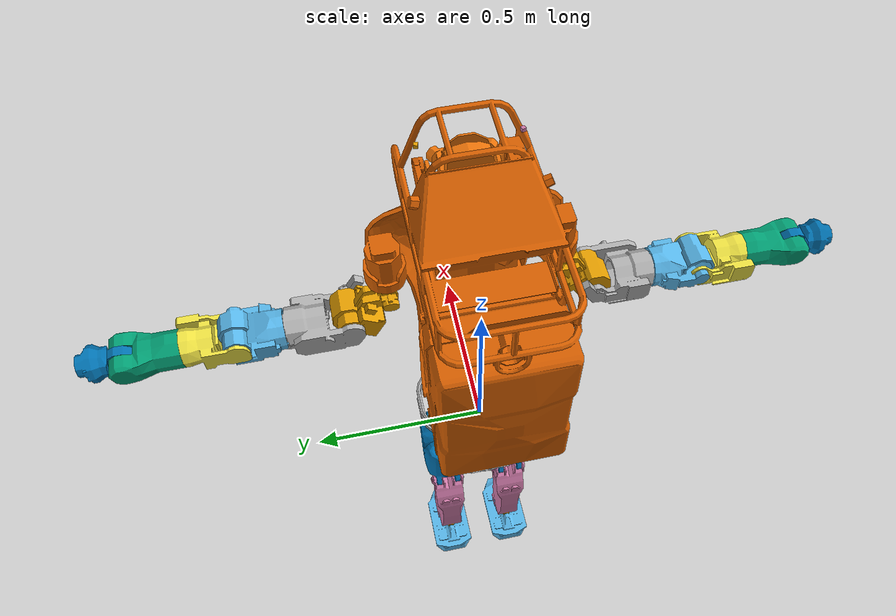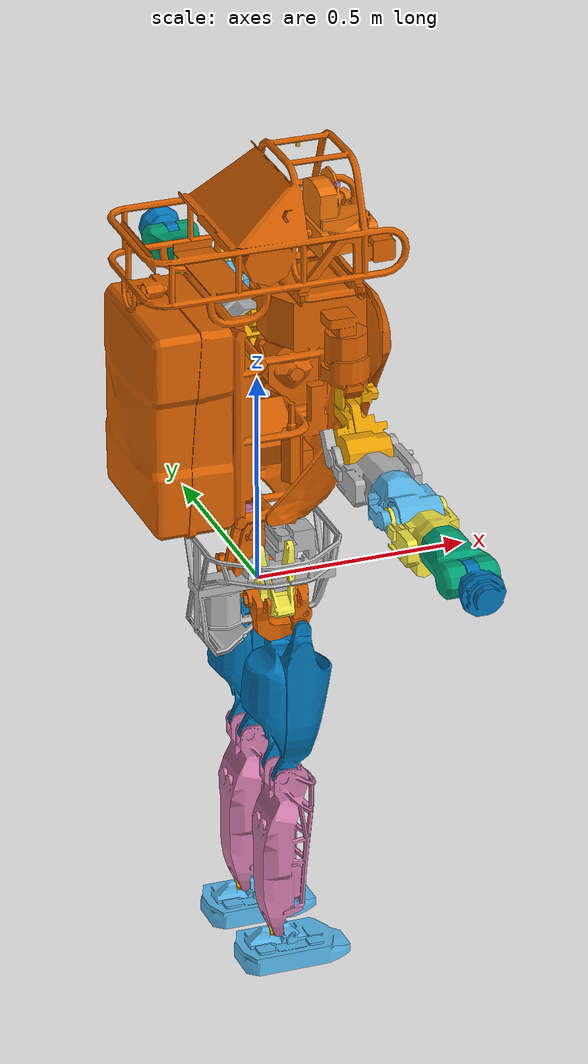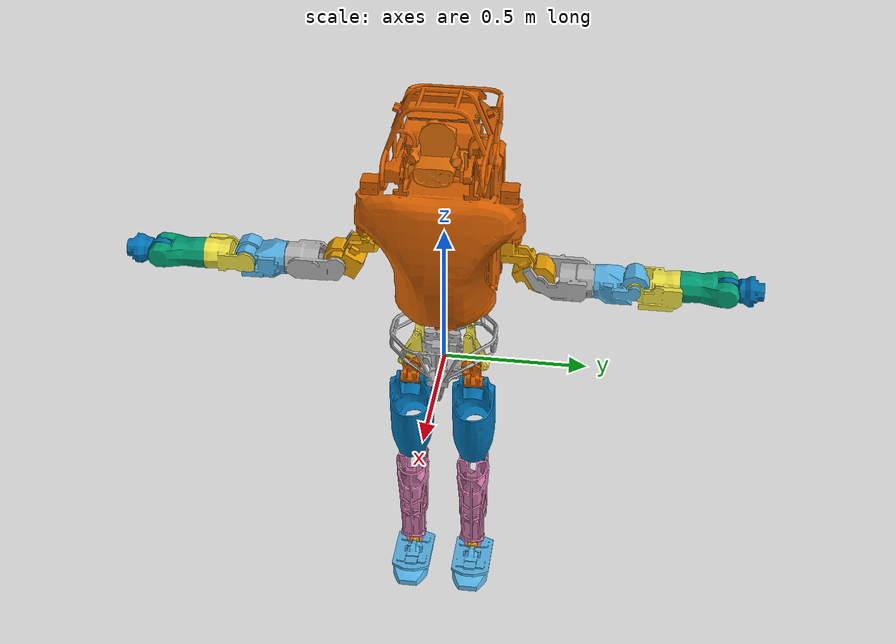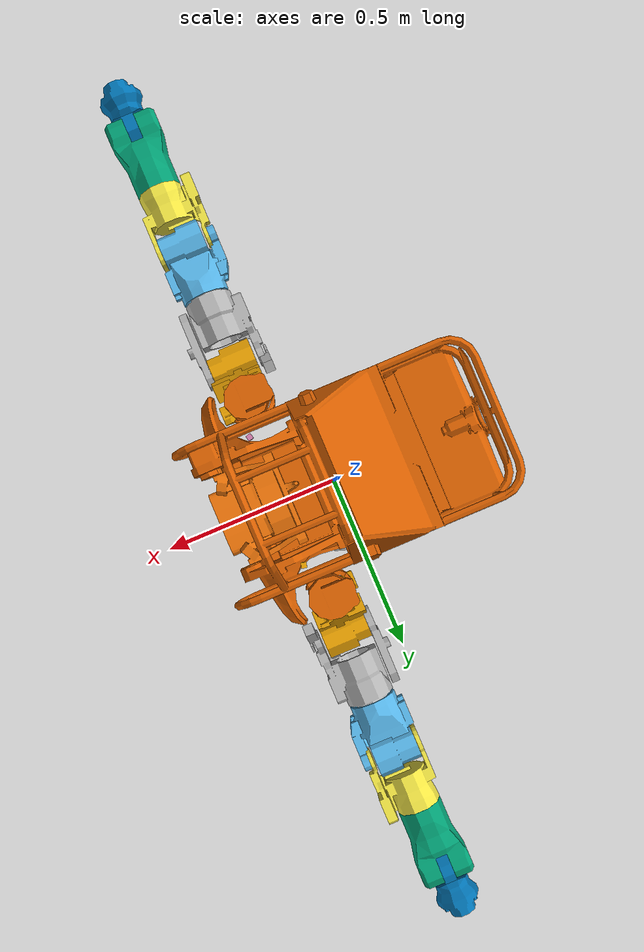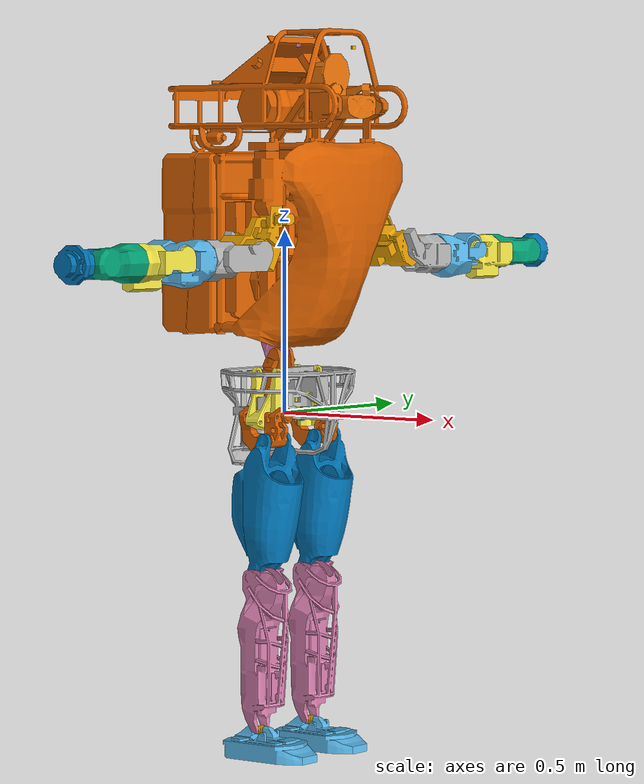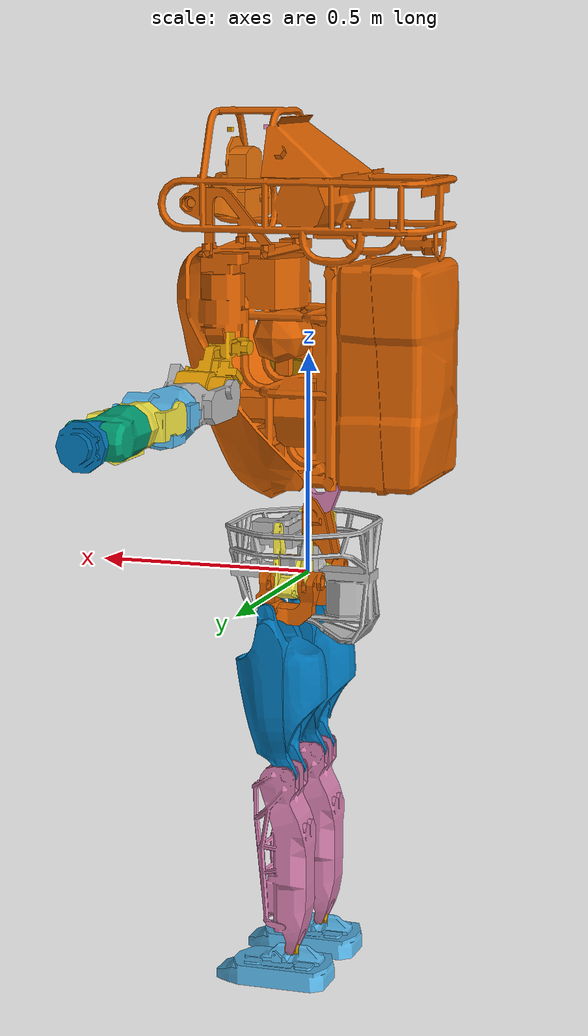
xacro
<?xml version="1.0" ?>
<!-- |    This document was autogenerated by xacro from src/drcsim_drcsim4_release/atlas_description/robots/atlas_v5.urdf.xacro | -->
<!-- |    EDITING THIS FILE BY HAND IS NOT RECOMMENDED                                 | -->
<robot name="atlas" xmlns:xacro="http://www.ros.org/wiki/xacro">
  <link name="l_clav">
    <inertial>
      <mass value="4.466"/>
      <origin rpy="0 0 0" xyz="0 0 -0.084"/>
      <inertia ixx="0.011" ixy="0" ixz="0" iyy="0.009" iyz="0.004" izz="0.004"/>
    </inertial>
    <visual>
      <geometry>
        <mesh filename="package://atlas_description/meshes_unplugged/r_clav.dae"/>
      </geometry>
    </visual>
    <collision>
      <origin rpy="0 1.5707963267949 0" xyz="0 -0.11 -0.248"/>
      <geometry>
        <cylinder length="0.1525" radius="0.0555"/>
      </geometry>
    </collision>
    <collision>
      <origin rpy="0 0 0" xyz="0.005 -0.015 -0.08"/>
      <geometry>
        <cylinder length="0.26" radius="0.067"/>
      </geometry>
    </collision>
    <collision>
      <origin rpy="1.05 0 0" xyz="0.004 -0.064 -0.247"/>
      <geometry>
        <box size="0.1 0.07 0.072"/>
      </geometry>
    </collision>
  </link>
  <link name="l_foot">
    <inertial>
      <mass value="2.410"/>
      <origin rpy="0 0 0" xyz="0.027 0 -0.067"/>
      <inertia ixx="0.002" ixy="0" ixz="0" iyy="0.007" iyz="0" izz="0.008"/>
    </inertial>
    <visual>
      <geometry>
        <mesh filename="package://atlas_description/meshes_unplugged/l_foot.dae"/>
      </geometry>
    </visual>
    <collision>
      <origin rpy="0 0 0" xyz="0.023 0 -0.049119"/>
      <geometry>
        <box size="0.227 0.133887 0.05"/>
      </geometry>
    </collision>
    <collision>
      <origin rpy="0 0 0" xyz="0.1225 0 -0.0641"/>
      <geometry>
        <box size="0.1 0.08 0.02"/>
      </geometry>
    </collision>
  </link>
  <link name="l_hand">
    <inertial>
      <mass value="0.5839"/>
      <origin rpy="0 0 0" xyz="0.00016 -0.08159 0.00002"/>
      <inertia ixx="0.000388" ixy="0" ixz="0" iyy="0.000477" iyz="0" izz="0.000379"/>
    </inertial>
  </link>
  <link name="l_larm">
    <inertial>
      <mass value="3.248"/>
      <origin rpy="0 0 0" xyz="0 0 0"/>
      <inertia ixx="0.00265" ixy="0" ixz="0" iyy="0.00446" iyz="0" izz="0.00446"/>
    </inertial>
    <visual>
      <geometry>
        <mesh filename="package://atlas_description/meshes_unplugged/r_larm.dae"/>
      </geometry>
    </visual>
    <collision>
      <origin rpy="-1.5707963267949 0 0" xyz="0.00 -0.075 -0.01"/>
      <geometry>
        <cylinder length="0.04" radius="0.051"/>
      </geometry>
    </collision>
    <collision>
      <origin rpy="0 1.5707963267949 0" xyz="-0.012 0 0.0025"/>
      <geometry>
        <cylinder length="0.147" radius="0.045"/>
      </geometry>
    </collision>
    <collision>
      <origin rpy="0 0 0" xyz="-0.07 -0.077 -0.015"/>
      <geometry>
        <box size="0.025 0.155 0.07"/>
      </geometry>
    </collision>
    <collision>
      <origin rpy="0 0 0" xyz="0.05 -0.067 -0.009"/>
      <geometry>
        <box size="0.025 0.06 0.06"/>
      </geometry>
    </collision>
    <collision>
      <origin rpy="0 0 0" xyz="-0.032 -0.071 -0.06"/>
      <geometry>
        <box size="0.04 0.115 0.05"/>
      </geometry>
    </collision>
    <collision>
      <origin rpy="0 0 0" xyz="0.03 0.01 -0.05"/>
      <geometry>
        <box size="0.045 0.055 0.023"/>
      </geometry>
    </collision>
  </link>
  <link name="l_lfarm">
    <inertial>
      <mass value="0.648"/>
      <origin rpy="0 0 0" xyz="0.00017 -0.02515 0.00163"/>
      <inertia ixx="0.000764" ixy="0" ixz="0" iyy="0.000429" iyz="0" izz="0.000825"/>
    </inertial>
    <visual>
      <origin rpy="0 3.14159265359 0" xyz="0 0 0"/>
      <geometry>
        <mesh filename="package://atlas_description/meshes_unplugged/r_hand.dae"/>
      </geometry>
    </visual>
    <collision>
      <origin rpy="1.5707963267949 0 0" xyz="0.00 -0.104 0.00"/>
      <geometry>
        <cylinder length="0.02" radius="0.031"/>
      </geometry>
    </collision>
    <collision>
      <origin rpy="1.5707963267949 0 0" xyz="0.00 -0.087 0.00"/>
      <geometry>
        <cylinder length="0.015" radius="0.045"/>
      </geometry>
    </collision>
    <collision>
      <origin rpy="1.5707963267949 0 0" xyz="0.00 -0.075 0.00"/>
      <geometry>
        <cylinder length="0.015" radius="0.052"/>
      </geometry>
    </collision>
    <collision>
      <origin rpy="1.5707963267949 0 0" xyz="0.00 -0.052 0.00"/>
      <geometry>
        <cylinder length="0.027" radius="0.043"/>
      </geometry>
    </collision>
  </link>
  <link name="l_lglut">
    <inertial>
      <mass value="0.898"/>
      <origin rpy="0 0 0" xyz="0.0133341 0.0170484 -0.0312052"/>
      <inertia ixx="0.000691326" ixy="-2.24344e-05" ixz="2.50508e-06" iyy="0.00126856" iyz="0.000137862" izz="0.00106487"/>
    </inertial>
    <visual>
      <geometry>
        <mesh filename="package://atlas_description/meshes_unplugged/l_lglut.dae"/>
      </geometry>
    </visual>
    <collision>
      <origin rpy="0 0 0" xyz="0.015 0.026 -0.028"/>
      <geometry>
        <box size="0.125 0.05 0.08"/>
      </geometry>
    </collision>
    <collision>
      <origin rpy="1.5707963267949 0 0" xyz="0.05 0.027488 -0.067"/>
      <geometry>
        <cylinder length="0.060306" radius="0.02009687"/>
      </geometry>
    </collision>
    <collision>
      <origin rpy="0 1.5707963267949 0" xyz="0.0115 0 0"/>
      <geometry>
        <cylinder length="0.144" radius="0.02"/>
      </geometry>
    </collision>
    <collision>
      <origin rpy="0 0 0" xyz="0.01 0.02 0.01"/>
      <geometry>
        <box size="0.0975 0.069 0.103"/>
      </geometry>
    </collision>
  </link>
  <link name="l_lleg">
    <inertial>
      <mass value="4.515"/>
      <origin rpy="0 0 0" xyz="0.001 0 -0.187"/>
      <inertia ixx="0.077" ixy="0" ixz="-0.003" iyy="0.076" iyz="0" izz="0.01"/>
    </inertial>
    <visual>
      <geometry>
        <mesh filename="package://atlas_description/meshes_unplugged/l_lleg.dae"/>
      </geometry>
    </visual>
    <collision>
      <origin rpy="0 0.10 0" xyz="0.02 0.00295 -0.182"/>
      <geometry>
        <cylinder length="0.40" radius="0.07"/>
      </geometry>
    </collision>
  </link>
  <link name="l_scap">
    <inertial>
      <mass value="3.899"/>
      <origin rpy="0 0 0" xyz="0 0 0"/>
      <inertia ixx="0.00319" ixy="0" ixz="0" iyy="0.00583" iyz="0" izz="0.00583"/>
    </inertial>
    <visual>
      <geometry>
        <mesh filename="package://atlas_description/meshes_unplugged/r_scap.dae"/>
      </geometry>
    </visual>
    <collision>
      <origin rpy="1.5707963267949 0 0" xyz="-0.005 -0.115 -0.014"/>
      <geometry>
        <cylinder length="0.105" radius="0.057"/>
      </geometry>
    </collision>
    <collision>
      <origin rpy="0 0 0" xyz="-0.005 -0.075 -0.015"/>
      <geometry>
        <box size="0.16 0.17 0.08"/>
      </geometry>
    </collision>
    <collision>
      <origin rpy="2.25 0 0" xyz="0.076 -0.0615 0.0128"/>
      <geometry>
        <box size="0.02 0.029 0.018"/>
      </geometry>
    </collision>
    <collision>
      <origin rpy="1 0 0" xyz="-0.075 0.015 0.019"/>
      <geometry>
        <box size="0.028 0.090 0.05"/>
      </geometry>
    </collision>
  </link>
  <link name="l_talus">
    <inertial>
      <mass value="0.125"/>
      <origin rpy="0 0 0" xyz="0 0 0"/>
      <inertia ixx="1.01674e-05" ixy="0" ixz="0" iyy="8.42775e-06" iyz="0" izz="1.30101e-05"/>
    </inertial>
    <visual>
      <geometry>
        <mesh filename="package://atlas_description/meshes_unplugged/l_talus.dae"/>
      </geometry>
    </visual>
    <collision>
      <origin rpy="0 1.5707963267949 0" xyz="0 0 0"/>
      <geometry>
        <cylinder length="0.029542" radius="0.010181"/>
      </geometry>
    </collision>
    <collision>
      <origin rpy="1.5707963267949 0 0" xyz="0 0 0"/>
      <geometry>
        <cylinder length="0.010059" radius="0.010348"/>
      </geometry>
    </collision>
  </link>
  <link name="l_uarm">
    <inertial>
      <mass value="4.386"/>
      <origin rpy="0 0 0" xyz="0 0.065 0"/>
      <inertia ixx="0.00656" ixy="0" ixz="0" iyy="0.00358" iyz="0" izz="0.00656"/>
    </inertial>
    <visual>
      <geometry>
        <mesh filename="package://atlas_description/meshes_unplugged/r_uarm.dae"/>
      </geometry>
    </visual>
    <collision>
      <origin rpy="1.5708 0 0" xyz="0.0 -0.035 -0.005"/>
      <geometry>
        <cylinder length="0.11" radius="0.065"/>
      </geometry>
    </collision>
    <collision>
      <origin rpy="0 1.5707963267949 0" xyz="-0.01 -0.043 0.002"/>
      <geometry>
        <box size="0.05 0.07 0.15"/>
      </geometry>
    </collision>
  </link>
  <link name="l_ufarm">
    <inertial>
      <mass value="2.4798"/>
      <origin rpy="0 0 0" xyz="0.00015 0.08296 0.00037"/>
      <inertia ixx="0.012731" ixy="0" ixz="0" iyy="0.002857" iyz="0" izz="0.011948"/>
    </inertial>
    <visual>
      <geometry>
        <mesh filename="package://atlas_description/meshes_unplugged/r_farm.dae"/>
      </geometry>
    </visual>
    <collision>
      <origin rpy="1.57 0 0" xyz="0 0.15 0"/>
      <geometry>
        <cylinder length="0.1" radius="0.053"/>
      </geometry>
    </collision>
    <collision>
      <origin rpy="0 1.5707963267949 0" xyz="-0.001 0.07 0.0"/>
      <geometry>
        <box size="0.08 0.09 0.11"/>
      </geometry>
    </collision>
    <collision>
      <origin rpy="0 1.57 0" xyz="0 0.005 0"/>
      <geometry>
        <cylinder length="0.125" radius="0.040"/>
      </geometry>
    </collision>
  </link>
  <link name="l_uglut">
    <inertial>
      <mass value="1.959"/>
      <origin rpy="0 0 0" xyz="0.00529262 -0.00344732 0.00313046"/>
      <inertia ixx="0.00074276" ixy="-3.79607e-08" ixz="-2.79549e-05" iyy="0.000688179" iyz="-3.2735e-08" izz="0.00041242"/>
    </inertial>
    <visual>
      <geometry>
        <mesh filename="package://atlas_description/meshes_unplugged/l_uglut.dae"/>
      </geometry>
    </visual>
    <collision>
      <origin rpy="0.52539 0 0" xyz="0.01 0.005 0"/>
      <geometry>
        <box size="0.05 0.1 0.1"/>
      </geometry>
    </collision>
    <collision>
      <origin rpy="0 0 0" xyz="0 0 0"/>
      <geometry>
        <cylinder length="0.080842" radius="0.019841"/>
      </geometry>
    </collision>
  </link>
  <link name="l_uleg">
    <inertial>
      <mass value="8.204"/>
      <origin rpy="0 0 0" xyz="0 0 -0.21"/>
      <inertia ixx="0.09" ixy="0" ixz="0" iyy="0.09" iyz="0" izz="0.02"/>
    </inertial>
    <visual>
      <geometry>
        <mesh filename="package://atlas_description/meshes_unplugged/l_uleg.dae"/>
      </geometry>
    </visual>
    <collision>
      <origin rpy="0 0 0" xyz="-0.0199 0.00585 -0.122"/>
      <geometry>
        <cylinder length="0.15" radius="0.09"/>
      </geometry>
    </collision>
    <collision>
      <origin rpy="0 -0.3 0" xyz="-0.032 -0.005 -0.224"/>
      <geometry>
        <cylinder length="0.15" radius="0.07"/>
      </geometry>
    </collision>
    <!-- to cover the logo shield -->
    <collision>
      <origin rpy="-0.15 0.13 0" xyz="0.003 0.015 -0.254"/>
      <geometry>
        <cylinder length="0.15" radius="0.05"/>
      </geometry>
    </collision>
    <!-- inside strut -->
    <collision>
      <origin rpy="0.0 0.0 0" xyz="-0.007 -0.053 -0.052"/>
      <geometry>
        <box size="0.07 0.038 0.15"/>
      </geometry>
    </collision>
    <!-- outside strut -->
    <collision>
      <origin rpy="0.0 0.0 0" xyz="-0.017 0.0595 -0.049"/>
      <geometry>
        <box size="0.07 0.038 0.14"/>
      </geometry>
    </collision>
  </link>
  <link name="ltorso">
    <inertial>
      <mass value="2.270"/>
      <origin rpy="0 0 0" xyz="-0.0112984 -3.15366e-06 0.0746835"/>
      <inertia ixx="0.0039092" ixy="-5.04491e-08" ixz="-0.000342157" iyy="0.00341694" iyz="4.87119e-07" izz="0.00174492"/>
    </inertial>
    <visual>
      <geometry>
        <mesh filename="package://atlas_description/meshes_unplugged/ltorso.dae"/>
      </geometry>
    </visual>
  </link>
  <link name="mtorso">
    <inertial>
      <mass value="0.799"/>
      <origin rpy="0 0 0" xyz="-0.00816266 -0.0131245 0.0305974"/>
      <inertia ixx="0.000454181" ixy="-6.10764e-05" ixz="3.94009e-05" iyy="0.000483282" iyz="5.27463e-05" izz="0.000444215"/>
    </inertial>
    <visual>
      <geometry>
        <mesh filename="package://atlas_description/meshes_unplugged/mtorso.dae"/>
      </geometry>
    </visual>
    <collision>
      <origin rpy="0 0 0" xyz="0.0 0 -0.02"/>
      <geometry>
        <cylinder length="0.15" radius="0.02"/>
      </geometry>
    </collision>
  </link>
  <link name="pelvis">
    <inertial>
      <mass value="9.509"/>
      <origin rpy="0 0 0" xyz="0.0111 0 0.0271"/>
      <inertia ixx="0.1244" ixy="0.0008" ixz="-0.0007" iyy="0.0958" iyz="-0.0005" izz="0.1167"/>
    </inertial>
    <visual>
      <geometry>
        <mesh filename="package://atlas_description/meshes_unplugged/pelvis.dae"/>
      </geometry>
    </visual>
    <collision>
      <origin rpy="1.5707963267949 0 0" xyz="0.046 0.0 0.01"/>
      <geometry>
        <cylinder length="0.06" radius="0.11"/>
      </geometry>
    </collision>
    <collision>
      <origin rpy="1.5707963267949 0 0" xyz="-0.03 0.0 0.01"/>
      <geometry>
        <cylinder length="0.06" radius="0.11"/>
      </geometry>
    </collision>
    <collision>
      <origin rpy="0 0 0" xyz="0.01 0.042 0.09"/>
      <geometry>
        <cylinder length="0.05" radius="0.16"/>
      </geometry>
    </collision>
    <collision>
      <origin rpy="0 0 0" xyz="0.01 -0.042 0.09"/>
      <geometry>
        <cylinder length="0.05" radius="0.16"/>
      </geometry>
    </collision>
    <collision>
      <origin rpy="0 0 0" xyz="-0.1 0 -0.02"/>
      <geometry>
        <box size="0.1 0.15 0.2"/>
      </geometry>
    </collision>
  </link>
  <link name="r_clav">
    <inertial>
      <mass value="4.466"/>
      <origin rpy="0 0 0" xyz="0 0 -0.084"/>
      <inertia ixx="0.011" ixy="0" ixz="0" iyy="0.009" iyz="0.004" izz="0.004"/>
    </inertial>
    <visual>
      <geometry>
        <mesh filename="package://atlas_description/meshes_unplugged/r_clav.dae"/>
      </geometry>
    </visual>
    <collision>
      <origin rpy="0 1.5707963267949 0" xyz="0 -0.11 -0.248"/>
      <geometry>
        <cylinder length="0.1525" radius="0.0555"/>
      </geometry>
    </collision>
    <collision>
      <origin rpy="0 0 0" xyz="0.005 -0.015 -0.08"/>
      <geometry>
        <cylinder length="0.26" radius="0.067"/>
      </geometry>
    </collision>
    <collision>
      <origin rpy="1.05 0 0" xyz="0.004 -0.064 -0.247"/>
      <geometry>
        <box size="0.1 0.07 0.072"/>
      </geometry>
    </collision>
  </link>
  <link name="r_foot">
    <inertial>
      <mass value="2.41"/>
      <origin rpy="0 0 0" xyz="0.027 0 -0.067"/>
      <inertia ixx="0.002" ixy="0" ixz="0" iyy="0.007" iyz="0" izz="0.008"/>
    </inertial>
    <visual>
      <geometry>
        <mesh filename="package://atlas_description/meshes_unplugged/r_foot.dae"/>
      </geometry>
    </visual>
    <collision>
      <origin rpy="0 0 0" xyz="0.023 0 -0.049119"/>
      <geometry>
        <box size="0.227 0.133887 0.05"/>
      </geometry>
    </collision>
    <collision>
      <origin rpy="0 0 0" xyz="0.1225 0 -0.0641"/>
      <geometry>
        <box size="0.1 0.08 0.02"/>
      </geometry>
    </collision>
  </link>
  <link name="r_hand">
    <inertial>
      <mass value="0.5839"/>
      <origin rpy="0 0 0" xyz="0.00016 -0.08159 0.00002"/>
      <inertia ixx="0.000388" ixy="0" ixz="0" iyy="0.000477" iyz="0" izz="0.000379"/>
    </inertial>
  </link>
  <link name="r_larm">
    <inertial>
      <mass value="3.248"/>
      <origin rpy="0 0 0" xyz="0 0 0"/>
      <inertia ixx="0.00265" ixy="0" ixz="0" iyy="0.00446" iyz="0" izz="0.00446"/>
    </inertial>
    <visual>
      <geometry>
        <mesh filename="package://atlas_description/meshes_unplugged/r_larm.dae"/>
      </geometry>
    </visual>
    <collision>
      <origin rpy="-1.5707963267949 0 0" xyz="0.00 -0.075 -0.01"/>
      <geometry>
        <cylinder length="0.04" radius="0.051"/>
      </geometry>
    </collision>
    <collision>
      <origin rpy="0 1.5707963267949 0" xyz="-0.012 0 0.0025"/>
      <geometry>
        <cylinder length="0.147" radius="0.045"/>
      </geometry>
    </collision>
    <collision>
      <origin rpy="0 0 0" xyz="-0.07 -0.077 -0.015"/>
      <geometry>
        <box size="0.025 0.155 0.07"/>
      </geometry>
    </collision>
    <collision>
      <origin rpy="0 0 0" xyz="0.05 -0.067 -0.009"/>
      <geometry>
        <box size="0.025 0.06 0.06"/>
      </geometry>
    </collision>
    <collision>
      <origin rpy="0 0 0" xyz="-0.032 -0.071 -0.06"/>
      <geometry>
        <box size="0.04 0.115 0.05"/>
      </geometry>
    </collision>
    <collision>
      <origin rpy="0 0 0" xyz="0.03 0.01 -0.05"/>
      <geometry>
        <box size="0.045 0.055 0.023"/>
      </geometry>
    </collision>
  </link>
  <link name="r_lfarm">
    <inertial>
      <mass value="0.648"/>
      <origin rpy="0 0 0" xyz="0.00017 -0.02515 0.00163"/>
      <inertia ixx="0.000764" ixy="0" ixz="0" iyy="0.000429" iyz="0" izz="0.000825"/>
    </inertial>
    <visual>
      <origin rpy="0 3.14159265359 0" xyz="0 0 0"/>
      <geometry>
        <mesh filename="package://atlas_description/meshes_unplugged/r_hand.dae"/>
      </geometry>
    </visual>
    <collision>
      <origin rpy="1.5707963267949 0 0" xyz="0.00 -0.104 0.00"/>
      <geometry>
        <cylinder length="0.02" radius="0.031"/>
      </geometry>
    </collision>
    <collision>
      <origin rpy="1.5707963267949 0 0" xyz="0.00 -0.087 0.00"/>
      <geometry>
        <cylinder length="0.015" radius="0.045"/>
      </geometry>
    </collision>
    <collision>
      <origin rpy="1.5707963267949 0 0" xyz="0.00 -0.075 0.00"/>
      <geometry>
        <cylinder length="0.015" radius="0.052"/>
      </geometry>
    </collision>
    <collision>
      <origin rpy="1.5707963267949 0 0" xyz="0.00 -0.052 0.00"/>
      <geometry>
        <cylinder length="0.027" radius="0.043"/>
      </geometry>
    </collision>
  </link>
  <link name="r_lglut">
    <inertial>
      <mass value="0.898"/>
      <origin rpy="0 0 0" xyz="0.0133341 -0.0170484 -0.0312052"/>
      <inertia ixx="0.000691326" ixy="2.24344e-05" ixz="2.50508e-06" iyy="0.00126856" iyz="-0.000137862" izz="0.00106487"/>
    </inertial>
    <visual>
      <geometry>
        <mesh filename="package://atlas_description/meshes_unplugged/r_lglut.dae"/>
      </geometry>
    </visual>
    <collision>
      <origin rpy="0 0 0" xyz="0.015 -0.026 -0.028"/>
      <geometry>
        <box size="0.125 0.05 0.08"/>
      </geometry>
    </collision>
    <collision>
      <origin rpy="1.5707963267949 0 0" xyz="0.05 -0.027488 -0.067"/>
      <geometry>
        <cylinder length="0.060306" radius="0.02009687"/>
      </geometry>
    </collision>
    <collision>
      <origin rpy="0 1.5707963267949 0" xyz="0.0105 0 0"/>
      <geometry>
        <cylinder length="0.142" radius="0.02"/>
      </geometry>
    </collision>
    <collision>
      <origin rpy="0 0 0" xyz="0.01 -0.02 0.01"/>
      <geometry>
        <box size="0.0975 0.069 0.103"/>
      </geometry>
    </collision>
  </link>
  <link name="r_lleg">
    <inertial>
      <mass value="4.515"/>
      <origin rpy="0 0 0" xyz="0.001 0 -0.187"/>
      <inertia ixx="0.077" ixy="-0" ixz="-0.003" iyy="0.076" iyz="-0" izz="0.01"/>
    </inertial>
    <visual>
      <geometry>
        <mesh filename="package://atlas_description/meshes_unplugged/r_lleg.dae"/>
      </geometry>
    </visual>
    <collision>
      <origin rpy="0 0.10 0" xyz="0.02 -0.00295 -0.182"/>
      <geometry>
        <cylinder length="0.40" radius="0.07"/>
      </geometry>
    </collision>
  </link>
  <link name="r_scap">
    <inertial>
      <mass value="3.899"/>
      <origin rpy="0 0 0" xyz="0 0 0"/>
      <inertia ixx="0.00319" ixy="0" ixz="0" iyy="0.00583" iyz="0" izz="0.00583"/>
    </inertial>
    <visual>
      <geometry>
        <mesh filename="package://atlas_description/meshes_unplugged/r_scap.dae"/>
      </geometry>
    </visual>
    <collision>
      <origin rpy="1.5707963267949 0 0" xyz="-0.005 -0.115 -0.014"/>
      <geometry>
        <cylinder length="0.105" radius="0.057"/>
      </geometry>
    </collision>
    <collision>
      <origin rpy="0 0 0" xyz="-0.005 -0.075 -0.015"/>
      <geometry>
        <box size="0.16 0.17 0.08"/>
      </geometry>
    </collision>
    <collision>
      <origin rpy="2.25 0 0" xyz="0.076 -0.0615 0.0128"/>
      <geometry>
        <box size="0.02 0.029 0.018"/>
      </geometry>
    </collision>
    <collision>
      <origin rpy="1 0 0" xyz="-0.075 0.015 0.019"/>
      <geometry>
        <box size="0.028 0.090 0.05"/>
      </geometry>
    </collision>
  </link>
  <link name="r_talus">
    <inertial>
      <mass value="0.125"/>
      <origin rpy="0 0 0" xyz="0 0 0"/>
      <inertia ixx="1.01674e-05" ixy="0" ixz="0" iyy="8.42775e-06" iyz="0" izz="1.30101e-05"/>
    </inertial>
    <visual>
      <geometry>
        <mesh filename="package://atlas_description/meshes_unplugged/r_talus.dae"/>
      </geometry>
    </visual>
    <collision>
      <origin rpy="0 1.5707963267949 0" xyz="0 0 0"/>
      <geometry>
        <cylinder length="0.029542" radius="0.010181"/>
      </geometry>
    </collision>
    <collision>
      <origin rpy="1.5707963267949 0 0" xyz="0 0 0"/>
      <geometry>
        <cylinder length="0.010059" radius="0.010348"/>
      </geometry>
    </collision>
  </link>
  <link name="r_uarm">
    <inertial>
      <mass value="4.386"/>
      <origin rpy="0 0 0" xyz="0 0.065 0"/>
      <inertia ixx="0.00656" ixy="0" ixz="0" iyy="0.00358" iyz="0" izz="0.00656"/>
    </inertial>
    <visual>
      <geometry>
        <mesh filename="package://atlas_description/meshes_unplugged/r_uarm.dae"/>
      </geometry>
    </visual>
    <collision>
      <origin rpy="1.5708 0 0" xyz="0.0 -0.035 -0.005"/>
      <geometry>
        <cylinder length="0.11" radius="0.065"/>
      </geometry>
    </collision>
    <collision>
      <origin rpy="0 1.5707963267949 0" xyz="-0.01 -0.043 0.002"/>
      <geometry>
        <box size="0.05 0.07 0.15"/>
      </geometry>
    </collision>
  </link>
  <link name="r_ufarm">
    <inertial>
      <mass value="2.4798"/>
      <origin rpy="0 0 0" xyz="0.00015 0.08296 0.00037"/>
      <inertia ixx="0.012731" ixy="0" ixz="0" iyy="0.002857" iyz="0" izz="0.011948"/>
    </inertial>
    <visual>
      <geometry>
        <mesh filename="package://atlas_description/meshes_unplugged/r_farm.dae"/>
      </geometry>
    </visual>
    <collision>
      <origin rpy="1.57 0 0" xyz="0 0.15 0"/>
      <geometry>
        <cylinder length="0.1" radius="0.053"/>
      </geometry>
    </collision>
    <collision>
      <origin rpy="0 1.5707963267949 0" xyz="-0.001 0.07 0.0"/>
      <geometry>
        <box size="0.08 0.09 0.11"/>
      </geometry>
    </collision>
    <collision>
      <origin rpy="0 1.57 0" xyz="0 0.005 0"/>
      <geometry>
        <cylinder length="0.125" radius="0.040"/>
      </geometry>
    </collision>
  </link>
  <link name="r_uglut">
    <inertial>
      <mass value="1.959"/>
      <origin rpy="0 0 0" xyz="0.00529262 0.00344732 0.00313046"/>
      <inertia ixx="0.00074276" ixy="3.79607e-08" ixz="-2.79549e-05" iyy="0.000688179" iyz="3.2735e-08" izz="0.00041242"/>
    </inertial>
    <visual>
      <geometry>
        <mesh filename="package://atlas_description/meshes_unplugged/r_uglut.dae"/>
      </geometry>
    </visual>
    <collision>
      <origin rpy="-0.52539 0 0" xyz="0.01 -0.005 0"/>
      <geometry>
        <box size="0.05 0.1 0.1"/>
      </geometry>
    </collision>
    <collision>
      <origin rpy="0 0 0" xyz="0 0 0"/>
      <geometry>
        <cylinder length="0.080842" radius="0.019841"/>
      </geometry>
    </collision>
  </link>
  <link name="r_uleg">
    <inertial>
      <mass value="8.204"/>
      <origin rpy="0 0 0" xyz="0 0 -0.21"/>
      <inertia ixx="0.09" ixy="0" ixz="0" iyy="0.09" iyz="0" izz="0.02"/>
    </inertial>
    <visual>
      <geometry>
        <mesh filename="package://atlas_description/meshes_unplugged/r_uleg.dae"/>
      </geometry>
    </visual>
    <collision>
      <origin rpy="0 0 0" xyz="-0.0199 -0.00585 -0.122"/>
      <geometry>
        <cylinder length="0.15" radius="0.09"/>
      </geometry>
    </collision>
    <collision>
      <origin rpy="0 -0.3 0" xyz="-0.032 0.005 -0.224"/>
      <geometry>
        <cylinder length="0.15" radius="0.07"/>
      </geometry>
    </collision>
    <!-- to cover the logo shield -->
    <collision>
      <origin rpy="0.15 0.13 0" xyz="0.003 -0.015 -0.254"/>
      <geometry>
        <cylinder length="0.15" radius="0.05"/>
      </geometry>
    </collision>
    <!-- inside strut -->
    <collision>
      <origin rpy="0.0 0.0 0" xyz="-0.007 0.053 -0.052"/>
      <geometry>
        <box size="0.07 0.038 0.15"/>
      </geometry>
    </collision>
    <!-- outside strut -->
    <collision>
      <origin rpy="0.0 0.0 0" xyz="-0.017 -0.0595 -0.049"/>
      <geometry>
        <box size="0.07 0.038 0.14"/>
      </geometry>
    </collision>
  </link>
  <link name="utorso">
    <inertial>
      <mass value="84.409"/>
      <origin rpy="0 0 0" xyz="-0.0622 0.0023 0.3157"/>
      <inertia ixx="1.577" ixy="-0.032" ixz="0.102" iyy="1.602" iyz="0.047" izz="0.565"/>
    </inertial>
    <visual>
      <geometry>
        <mesh filename="package://atlas_description/meshes_unplugged/utorso.dae"/>
      </geometry>
    </visual>
    <collision>
      <origin rpy="0 0 0" xyz="-0.102 0 0.25"/>
      <geometry>
        <box size="0.4 0.35 0.5"/>
      </geometry>
    </collision>
    <collision>
      <origin rpy="0 1.5707 0" xyz="0.2 0 0.46"/>
      <geometry>
        <box size="0.13 0.50 0.10"/>
      </geometry>
    </collision>
    <collision>
      <origin rpy="0 1.7 0" xyz="0.2 0 0.285"/>
      <geometry>
        <box size="0.2 0.23 0.10"/>
      </geometry>
    </collision>
    <collision>
      <origin rpy="0 2.0 0" xyz="0.15 0 0.10"/>
      <geometry>
        <box size="0.2 0.18 0.10"/>
      </geometry>
    </collision>
    <collision>
      <origin rpy="0 0 0" xyz="-0.035 0 0.6265"/>
      <geometry>
        <box size="0.506306 0.341719 0.12"/>
      </geometry>
    </collision>
    <collision>
      <origin rpy="1.5707 0 0" xyz="0.208 0 0.8215"/>
      <geometry>
        <cylinder length="0.13" radius="0.008"/>
      </geometry>
    </collision>
    <collision>
      <origin rpy="-0.38535 0 0" xyz="0.208 -0.125 0.745"/>
      <geometry>
        <cylinder length="0.15" radius="0.008"/>
      </geometry>
    </collision>
    <collision>
      <origin rpy="0.38535 0 0" xyz="0.208 0.125 0.745"/>
      <geometry>
        <cylinder length="0.15" radius="0.008"/>
      </geometry>
    </collision>
    <collision>
      <origin rpy="-0.38535 0 0" xyz="0.063 -0.125 0.745"/>
      <geometry>
        <cylinder length="0.15" radius="0.008"/>
      </geometry>
    </collision>
    <collision>
      <origin rpy="0.38535 0 0" xyz="0.063 0.125 0.745"/>
      <geometry>
        <cylinder length="0.15" radius="0.008"/>
      </geometry>
    </collision>
    <collision>
      <origin rpy="1.5707 0 1.5707" xyz="0.14 0.06 0.8215"/>
      <geometry>
        <cylinder length="0.15" radius="0.008"/>
      </geometry>
    </collision>
    <collision>
      <origin rpy="1.5707 0 1.5707" xyz="0.14 -0.06 0.8215"/>
      <geometry>
        <cylinder length="0.15" radius="0.008"/>
      </geometry>
    </collision>
    <collision>
      <origin rpy="0 -0.65 0" xyz="-0.029 0 0.731"/>
      <geometry>
        <box size="0.2 0.25 0.01"/>
      </geometry>
    </collision>
    <collision>
      <origin rpy="1.5707 0 0" xyz="0.063 0 0.8215"/>
      <geometry>
        <cylinder length="0.13" radius="0.008"/>
      </geometry>
    </collision>
    <collision>
      <origin rpy="1.5707 0 0" xyz="0.261 0.156 0.6215"/>
      <geometry>
        <cylinder length="0.016" radius="0.055"/>
      </geometry>
    </collision>
    <collision>
      <origin rpy="1.5707 0 0" xyz="0.261 -0.156 0.6215"/>
      <geometry>
        <cylinder length="0.016" radius="0.055"/>
      </geometry>
    </collision>
  </link>
  <joint name="back_bkx" type="revolute">
    <origin rpy="0 0 0" xyz="0 0 0.05"/>
    <axis xyz="1 0 0"/>
    <parent link="mtorso"/>
    <child link="utorso"/>
    <dynamics damping="0.1" friction="0"/>
    <limit effort="300" lower="-0.523599" upper="0.523599" velocity="12"/>
    <safety_controller k_position="100" k_velocity="100" soft_lower_limit="-10.5236" soft_upper_limit="10.5236"/>
  </joint>
  <joint name="back_bky" type="revolute">
    <origin rpy="0 0 0" xyz="0 0 0.162"/>
    <axis xyz="0 1 0"/>
    <parent link="ltorso"/>
    <child link="mtorso"/>
    <dynamics damping="0.1" friction="0"/>
    <limit effort="445" lower="-0.219388" upper="0.538783" velocity="9"/>
    <safety_controller k_position="100" k_velocity="100" soft_lower_limit="-10.2194" soft_upper_limit="10.5388"/>
  </joint>
  <joint name="back_bkz" type="revolute">
    <origin rpy="0 0 0" xyz="-0.0125 0 0"/>
    <axis xyz="0 0 1"/>
    <parent link="pelvis"/>
    <child link="ltorso"/>
    <dynamics damping="0.1" friction="0"/>
    <limit effort="106" lower="-0.663225" upper="0.663225" velocity="12"/>
    <safety_controller k_position="100" k_velocity="100" soft_lower_limit="-10.6632" soft_upper_limit="10.6632"/>
  </joint>
  <joint name="l_arm_elx" type="revolute">
    <origin rpy="0 0 0" xyz="0 -0.119 0.0092"/>
    <axis xyz="-1.0 -0.0 -0.0"/>
    <parent link="l_uarm"/>
    <child link="l_larm"/>
    <dynamics damping="0.1" friction="0"/>
    <limit effort="112" lower="0" upper="2.35619" velocity="12"/>
    <safety_controller k_position="100" k_velocity="100" soft_lower_limit="-10" soft_upper_limit="12.3562"/>
  </joint>
  <joint name="l_arm_ely" type="revolute">
    <origin rpy="0 0 0" xyz="0 -0.187 -0.016"/>
    <axis xyz="-0.0 -1.0 -0.0"/>
    <parent link="l_scap"/>
    <child link="l_uarm"/>
    <dynamics damping="0.1" friction="0"/>
    <limit effort="63" lower="0" upper="3.14159" velocity="12"/>
    <safety_controller k_position="100" k_velocity="100" soft_lower_limit="-10" soft_upper_limit="13.1416"/>
  </joint>
  <joint name="l_arm_shx" type="revolute">
    <origin rpy="0 0 0" xyz="0 -0.11 -0.245"/>
    <axis xyz="-1.0 -0.0 -0.0"/>
    <parent link="l_clav"/>
    <child link="l_scap"/>
    <dynamics damping="0.1" friction="0"/>
    <limit effort="99" lower="-1.5708" upper="1.5708" velocity="12"/>
    <safety_controller k_position="100" k_velocity="100" soft_lower_limit="-11.5708" soft_upper_limit="11.5708"/>
  </joint>
  <joint name="l_arm_shz" type="revolute">
    <origin rpy="0 0 3.14159265359" xyz="0.1406 0.2256 0.4776"/>
    <axis xyz="0 0 1"/>
    <parent link="utorso"/>
    <child link="l_clav"/>
    <dynamics damping="0.1" friction="0"/>
    <limit effort="87" lower="-1.5708" upper="0.785398" velocity="12"/>
    <safety_controller k_position="100" k_velocity="100" soft_lower_limit="-11.5708" soft_upper_limit="10.7854"/>
  </joint>
  <joint name="l_arm_wrx" type="revolute">
    <origin rpy="0 0 0" xyz="0 0 0"/>
    <axis xyz="1 0 0"/>
    <parent link="l_ufarm"/>
    <child link="l_lfarm"/>
    <dynamics damping="0.1" friction="0"/>
    <limit effort="25" lower="-1.7628" upper="1.7628" velocity="10"/>
    <safety_controller k_position="100" k_velocity="100" soft_lower_limit="-11.7628" soft_upper_limit="11.7628"/>
  </joint>
  <joint name="l_arm_wry" type="revolute">
    <origin rpy="0 3.14159265359 0" xyz="0 -0.29955 -0.00921"/>
    <axis xyz="-0.0 -1.0 -0.0"/>
    <parent link="l_larm"/>
    <child link="l_ufarm"/>
    <dynamics damping="0.1" friction="0"/>
    <limit effort="25" lower="-3.011" upper="3.011" velocity="10"/>
    <safety_controller k_position="100" k_velocity="100" soft_lower_limit="-13.011" soft_upper_limit="13.011"/>
  </joint>
  <joint name="l_arm_wry2" type="revolute">
    <origin rpy="0 3.14159265359 0" xyz="0 0 0"/>
    <axis xyz="0 1 0"/>
    <parent link="l_lfarm"/>
    <child link="l_hand"/>
    <dynamics damping="0.1" friction="0"/>
    <limit effort="25" lower="-2.9671" upper="2.9671" velocity="10"/>
    <safety_controller k_position="100" k_velocity="100" soft_lower_limit="-12.9671" soft_upper_limit="12.9671"/>
  </joint>
  <joint name="l_leg_akx" type="revolute">
    <origin rpy="0 0 0" xyz="0 0 0"/>
    <axis xyz="1 0 0"/>
    <parent link="l_talus"/>
    <child link="l_foot"/>
    <dynamics damping="0.1" friction="0"/>
    <limit effort="360" lower="-0.8" upper="0.8" velocity="12"/>
    <safety_controller k_position="100" k_velocity="100" soft_lower_limit="-10.8" soft_upper_limit="10.8"/>
  </joint>
  <joint name="l_leg_aky" type="revolute">
    <origin rpy="0 0 0" xyz="0 0 -0.422"/>
    <axis xyz="0 1 0"/>
    <parent link="l_lleg"/>
    <child link="l_talus"/>
    <dynamics damping="0.1" friction="0"/>
    <limit effort="740" lower="-1" upper="0.7" velocity="12"/>
    <safety_controller k_position="100" k_velocity="100" soft_lower_limit="-11" soft_upper_limit="10.7"/>
  </joint>
  <joint name="l_leg_hpx" type="revolute">
    <origin rpy="0 0 0" xyz="0 0 0"/>
    <axis xyz="1 0 0"/>
    <parent link="l_uglut"/>
    <child link="l_lglut"/>
    <dynamics damping="0.1" friction="0"/>
    <limit effort="530" lower="-0.523599" upper="0.523599" velocity="12"/>
    <safety_controller k_position="100" k_velocity="100" soft_lower_limit="-10.5236" soft_upper_limit="10.5236"/>
  </joint>
  <joint name="l_leg_hpy" type="revolute">
    <origin rpy="0 0 0" xyz="0.05 0.0225 -0.066"/>
    <axis xyz="0 1 0"/>
    <parent link="l_lglut"/>
    <child link="l_uleg"/>
    <dynamics damping="0.1" friction="0"/>
    <limit effort="840" lower="-1.61234" upper="0.65764" velocity="12"/>
    <safety_controller k_position="100" k_velocity="100" soft_lower_limit="-11.6123" soft_upper_limit="10.6576"/>
  </joint>
  <joint name="l_leg_hpz" type="revolute">
    <origin rpy="0 0 0" xyz="0 0.089 0"/>
    <axis xyz="0 0 1"/>
    <parent link="pelvis"/>
    <child link="l_uglut"/>
    <dynamics damping="0.1" friction="0"/>
    <limit effort="275" lower="-0.174358" upper="0.786794" velocity="12"/>
    <safety_controller k_position="100" k_velocity="100" soft_lower_limit="-10.1744" soft_upper_limit="10.7868"/>
  </joint>
  <joint name="l_leg_kny" type="revolute">
    <origin rpy="0 0 0" xyz="-0.05 0 -0.374"/>
    <axis xyz="0 1 0"/>
    <parent link="l_uleg"/>
    <child link="l_lleg"/>
    <dynamics damping="0.1" friction="0"/>
    <limit effort="890" lower="0" upper="2.35637" velocity="12"/>
    <safety_controller k_position="100" k_velocity="100" soft_lower_limit="-10" soft_upper_limit="12.3564"/>
  </joint>
  <joint name="neck_ry" type="revolute">
    <origin rpy="0 0 0" xyz="0.2546 0 0.6215"/>
    <axis xyz="0 1 0"/>
    <parent link="utorso"/>
    <child link="head"/>
    <dynamics damping="0.1" friction="0"/>
    <limit effort="25" lower="-0.602139" upper="1.14319" velocity="6.28"/>
    <safety_controller k_position="100" k_velocity="100" soft_lower_limit="-10.6021" soft_upper_limit="11.1432"/>
  </joint>
  <joint name="r_arm_elx" type="revolute">
    <origin rpy="0 0 0" xyz="0 -0.119 0.0092"/>
    <axis xyz="1 0 0"/>
    <parent link="r_uarm"/>
    <child link="r_larm"/>
    <dynamics damping="0.1" friction="0"/>
    <limit effort="112" lower="-2.35619" upper="0" velocity="12"/>
    <safety_controller k_position="100" k_velocity="100" soft_lower_limit="-12.3562" soft_upper_limit="10"/>
  </joint>
  <joint name="r_arm_ely" type="revolute">
    <origin rpy="0 0 0" xyz="0 -0.187 -0.016"/>
    <axis xyz="0 1 0"/>
    <parent link="r_scap"/>
    <child link="r_uarm"/>
    <dynamics damping="0.1" friction="0"/>
    <limit effort="63" lower="0" upper="3.14159" velocity="12"/>
    <safety_controller k_position="100" k_velocity="100" soft_lower_limit="-10" soft_upper_limit="13.1416"/>
  </joint>
  <joint name="r_arm_shx" type="revolute">
    <origin rpy="0 0 0" xyz="0 -0.11 -0.245"/>
    <axis xyz="1 0 0"/>
    <parent link="r_clav"/>
    <child link="r_scap"/>
    <dynamics damping="0.1" friction="0"/>
    <limit effort="99" lower="-1.5708" upper="1.5708" velocity="12"/>
    <safety_controller k_position="100" k_velocity="100" soft_lower_limit="-11.5708" soft_upper_limit="11.5708"/>
  </joint>
  <joint name="r_arm_shz" type="revolute">
    <origin rpy="0 0 0" xyz="0.1406 -0.2256 0.4776"/>
    <axis xyz="0 0 1"/>
    <parent link="utorso"/>
    <child link="r_clav"/>
    <dynamics damping="0.1" friction="0"/>
    <limit effort="87" lower="-0.785398" upper="1.5708" velocity="12"/>
    <safety_controller k_position="100" k_velocity="100" soft_lower_limit="-10.7854" soft_upper_limit="11.5708"/>
  </joint>
  <joint name="r_arm_wrx" type="revolute">
    <origin rpy="0 0 0" xyz="0 0 0"/>
    <axis xyz="1 0 0"/>
    <parent link="r_ufarm"/>
    <child link="r_lfarm"/>
    <dynamics damping="0.1" friction="0"/>
    <limit effort="25" lower="-1.7628" upper="1.7628" velocity="10"/>
    <safety_controller k_position="100" k_velocity="100" soft_lower_limit="-11.7628" soft_upper_limit="11.7628"/>
  </joint>
  <joint name="r_arm_wry" type="revolute">
    <origin rpy="0 0 0" xyz="0 -0.29955 -0.00921"/>
    <axis xyz="0 1 0"/>
    <parent link="r_larm"/>
    <child link="r_ufarm"/>
    <dynamics damping="0.1" friction="0"/>
    <limit effort="25" lower="-3.011" upper="3.011" velocity="10"/>
    <safety_controller k_position="100" k_velocity="100" soft_lower_limit="-13.011" soft_upper_limit="13.011"/>
  </joint>
  <joint name="r_arm_wry2" type="revolute">
    <origin rpy="0 0 0" xyz="0 0 0"/>
    <axis xyz="0 1 0"/>
    <parent link="r_lfarm"/>
    <child link="r_hand"/>
    <dynamics damping="0.1" friction="0"/>
    <limit effort="25" lower="-2.9671" upper="2.9671" velocity="10"/>
    <safety_controller k_position="100" k_velocity="100" soft_lower_limit="-12.9671" soft_upper_limit="12.9671"/>
  </joint>
  <joint name="r_leg_akx" type="revolute">
    <origin rpy="0 0 0" xyz="0 0 0"/>
    <axis xyz="1 0 0"/>
    <parent link="r_talus"/>
    <child link="r_foot"/>
    <dynamics damping="0.1" friction="0"/>
    <limit effort="360" lower="-0.8" upper="0.8" velocity="12"/>
    <safety_controller k_position="100" k_velocity="100" soft_lower_limit="-10.8" soft_upper_limit="10.8"/>
  </joint>
  <joint name="r_leg_aky" type="revolute">
    <origin rpy="0 0 0" xyz="0 0 -0.422"/>
    <axis xyz="0 1 0"/>
    <parent link="r_lleg"/>
    <child link="r_talus"/>
    <dynamics damping="0.1" friction="0"/>
    <limit effort="740" lower="-1" upper="0.7" velocity="12"/>
    <safety_controller k_position="100" k_velocity="100" soft_lower_limit="-11" soft_upper_limit="10.7"/>
  </joint>
  <joint name="r_leg_hpx" type="revolute">
    <origin rpy="0 0 0" xyz="0 0 0"/>
    <axis xyz="1 0 0"/>
    <parent link="r_uglut"/>
    <child link="r_lglut"/>
    <dynamics damping="0.1" friction="0"/>
    <limit effort="530" lower="-0.523599" upper="0.523599" velocity="12"/>
    <safety_controller k_position="100" k_velocity="100" soft_lower_limit="-10.5236" soft_upper_limit="10.5236"/>
  </joint>
  <joint name="r_leg_hpy" type="revolute">
    <origin rpy="0 0 0" xyz="0.05 -0.0225 -0.066"/>
    <axis xyz="0 1 0"/>
    <parent link="r_lglut"/>
    <child link="r_uleg"/>
    <dynamics damping="0.1" friction="0"/>
    <limit effort="840" lower="-1.61234" upper="0.65764" velocity="12"/>
    <safety_controller k_position="100" k_velocity="100" soft_lower_limit="-11.6123" soft_upper_limit="10.6576"/>
  </joint>
  <joint name="r_leg_hpz" type="revolute">
    <origin rpy="0 0 0" xyz="0 -0.089 0"/>
    <axis xyz="0 0 1"/>
    <parent link="pelvis"/>
    <child link="r_uglut"/>
    <dynamics damping="0.1" friction="0"/>
    <limit effort="275" lower="-0.786794" upper="0.174358" velocity="12"/>
    <safety_controller k_position="100" k_velocity="100" soft_lower_limit="-10.7868" soft_upper_limit="10.1744"/>
  </joint>
  <joint name="r_leg_kny" type="revolute">
    <origin rpy="0 0 0" xyz="-0.05 0 -0.374"/>
    <axis xyz="0 1 0"/>
    <parent link="r_uleg"/>
    <child link="r_lleg"/>
    <dynamics damping="0.1" friction="0"/>
    <limit effort="890" lower="0" upper="2.35637" velocity="12"/>
    <safety_controller k_position="100" k_velocity="100" soft_lower_limit="-10" soft_upper_limit="12.3564"/>
  </joint>
  <link name="r_situational_awareness_camera_link">
    <inertial>
      <mass value="0.1"/>
      <origin xyz="0 0 0"/>
      <inertia ixx="0.00001" ixy="0" ixz="0" iyy="0.00001" iyz="0" izz="0.00001"/>
    </inertial>
    <visual>
      <origin rpy="0 0 0" xyz="0 0 0"/>
      <geometry>
        <box size="0.01 0.01 0.01"/>
      </geometry>
    </visual>
  </link>
  <joint name="r_situational_awareness_camera_joint" type="fixed">
    <parent link="utorso"/>
    <child link="r_situational_awareness_camera_link"/>
    <!-- SA camera mounted above the multisense head -->
    <origin rpy="0 0 -1.309" xyz="0.155 -0.121 0.785"/>
  </joint>
  <joint name="r_situational_awareness_camera_optical_frame_joint" type="fixed">
    <origin rpy="-1.5708 0.0 -1.5708" xyz="0 0 0"/>
    <parent link="r_situational_awareness_camera_link"/>
    <child link="r_situational_awareness_camera_optical_frame"/>
  </joint>
  <link name="r_situational_awareness_camera_optical_frame"/>
  <link name="l_situational_awareness_camera_link">
    <inertial>
      <mass value="0.1"/>
      <origin xyz="0 0 0"/>
      <inertia ixx="0.00001" ixy="0" ixz="0" iyy="0.00001" iyz="0" izz="0.00001"/>
    </inertial>
    <visual>
      <origin rpy="0 0 0" xyz="0 0 0"/>
      <geometry>
        <box size="0.01 0.01 0.01"/>
      </geometry>
    </visual>
  </link>
  <joint name="l_situational_awareness_camera_joint" type="fixed">
    <parent link="utorso"/>
    <child link="l_situational_awareness_camera_link"/>
    <!-- SA camera mounted above the multisense head -->
    <origin rpy="0 0 1.309" xyz="0.155 0.121 0.785"/>
  </joint>
  <joint name="l_situational_awareness_camera_optical_frame_joint" type="fixed">
    <origin rpy="-1.5708 0.0 -1.5708" xyz="0 0 0"/>
    <parent link="l_situational_awareness_camera_link"/>
    <child link="l_situational_awareness_camera_optical_frame"/>
  </joint>
  <link name="l_situational_awareness_camera_optical_frame"/>
  <gazebo>
    <!-- robot model offset -->
    <pose>0 0 0.93 0 0 0</pose>
  </gazebo>
  <gazebo>
    <plugin filename="libAtlasV4Plugin.so" name="atlas_plugin"/>
    <plugin filename="libgazebo_ros_joint_pose_trajectory.so" name="joint_trajectory_plugin">
      <topicName>joint_trajectory</topicName>
      <updateRate>1000.0</updateRate>
    </plugin>
  </gazebo>
  <!-- imu -->
  <link name="imu_link">
    <inertial>
      <mass value="0.1"/>
      <origin xyz="0 0 0"/>
      <inertia ixx="0.001" ixy="0" ixz="0" iyy="0.001" iyz="0" izz="0.001"/>
    </inertial>
    <visual>
      <origin rpy="0 0 0" xyz="0 0 0"/>
      <geometry>
        <box size="0.01 0.01 0.01"/>
      </geometry>
    </visual>
  </link>
  <joint name="imu_joint" type="fixed">
    <parent link="pelvis"/>
    <child link="imu_link"/>
    <origin rpy="0 0 0" xyz="0.05991527603 0 -0.01415"/>
  </joint>
  <gazebo reference="imu_link">
    <!-- this is expected to be reparented to pelvis with appropriate offset
         when imu_link is reduced by fixed joint reduction -->
    <!-- todo: this is working with gazebo 1.4, need to write a unit test -->
    <sensor name="imu_sensor" type="imu">
      <always_on>1</always_on>
      <update_rate>1000.0</update_rate>
      <imu>
        <noise>
          <type>gaussian</type>
          <rate>
            <mean>0.0</mean>
            <stddev>2e-4</stddev>
            <bias_mean>0.0000075</bias_mean>
            <bias_stddev>0.0000008</bias_stddev>
          </rate>
          <accel>
            <mean>0.0</mean>
            <stddev>1.7e-2</stddev>
            <bias_mean>0.1</bias_mean>
            <bias_stddev>0.001</bias_stddev>
          </accel>
        </noise>
      </imu>
    </sensor>
  </gazebo>
  <gazebo reference="l_arm_wrx">
    <provideFeedback>1</provideFeedback>
  </gazebo>
  <gazebo reference="r_arm_wrx">
    <provideFeedback>1</provideFeedback>
  </gazebo>
  <gazebo reference="l_leg_akx">
    <provideFeedback>1</provideFeedback>
    <implicitSpringDamper>1</implicitSpringDamper>
  </gazebo>
  <gazebo reference="r_leg_akx">
    <provideFeedback>1</provideFeedback>
    <implicitSpringDamper>1</implicitSpringDamper>
  </gazebo>
  <gazebo reference="r_foot">
    <!-- kp and kd for rubber -->
    <kp>1000000.0</kp>
    <kd>100.0</kd>
    <mu1>1.5</mu1>
    <mu2>1.5</mu2>
    <fdir1>1 0 0</fdir1>
    <maxVel>1.0</maxVel>
    <minDepth>0.00</minDepth>
  </gazebo>
  <gazebo reference="l_foot">
    <kp>1000000.0</kp>
    <kd>100.0</kd>
    <mu1>1.5</mu1>
    <mu2>1.5</mu2>
    <fdir1>1 0 0</fdir1>
    <maxVel>1.0</maxVel>
    <minDepth>0.00</minDepth>
  </gazebo>
  <gazebo reference="l_clav">
    <mu1>0.9</mu1>
    <mu2>0.9</mu2>
  </gazebo>
  <gazebo reference="l_lfarm">
    <mu1>0.9</mu1>
    <mu2>0.9</mu2>
  </gazebo>
  <gazebo reference="l_ufarm">
    <mu1>0.9</mu1>
    <mu2>0.9</mu2>
  </gazebo>
  <gazebo reference="l_hand">
    <mu1>0.9</mu1>
    <mu2>0.9</mu2>
  </gazebo>
  <gazebo reference="l_larm">
    <mu1>0.9</mu1>
    <mu2>0.9</mu2>
  </gazebo>
  <gazebo reference="l_lglut">
    <mu1>0.9</mu1>
    <mu2>0.9</mu2>
  </gazebo>
  <gazebo reference="l_lleg">
    <mu1>0.9</mu1>
    <mu2>0.9</mu2>
  </gazebo>
  <gazebo reference="l_scap">
    <mu1>0.9</mu1>
    <mu2>0.9</mu2>
  </gazebo>
  <gazebo reference="l_talus">
    <mu1>0.9</mu1>
    <mu2>0.9</mu2>
  </gazebo>
  <gazebo reference="l_uarm">
    <mu1>0.9</mu1>
    <mu2>0.9</mu2>
  </gazebo>
  <gazebo reference="l_uglut">
    <mu1>0.9</mu1>
    <mu2>0.9</mu2>
  </gazebo>
  <gazebo reference="l_uleg">
    <mu1>0.9</mu1>
    <mu2>0.9</mu2>
  </gazebo>
  <gazebo reference="ltorso">
    <mu1>0.9</mu1>
    <mu2>0.9</mu2>
  </gazebo>
  <gazebo reference="mtorso">
    <mu1>0.9</mu1>
    <mu2>0.9</mu2>
  </gazebo>
  <gazebo reference="pelvis">
    <mu1>0.9</mu1>
    <mu2>0.9</mu2>
  </gazebo>
  <gazebo reference="r_clav">
    <mu1>0.9</mu1>
    <mu2>0.9</mu2>
  </gazebo>
  <gazebo reference="r_lfarm">
    <mu1>0.9</mu1>
    <mu2>0.9</mu2>
  </gazebo>
  <gazebo reference="r_ufarm">
    <mu1>0.9</mu1>
    <mu2>0.9</mu2>
  </gazebo>
  <gazebo reference="r_hand">
    <mu1>0.9</mu1>
    <mu2>0.9</mu2>
  </gazebo>
  <gazebo reference="r_larm">
    <mu1>0.9</mu1>
    <mu2>0.9</mu2>
  </gazebo>
  <gazebo reference="r_lglut">
    <mu1>0.9</mu1>
    <mu2>0.9</mu2>
  </gazebo>
  <gazebo reference="r_lleg">
    <mu1>0.9</mu1>
    <mu2>0.9</mu2>
  </gazebo>
  <gazebo reference="r_scap">
    <mu1>0.9</mu1>
    <mu2>0.9</mu2>
  </gazebo>
  <gazebo reference="r_talus">
    <mu1>0.9</mu1>
    <mu2>0.9</mu2>
  </gazebo>
  <gazebo reference="r_uarm">
    <mu1>0.9</mu1>
    <mu2>0.9</mu2>
  </gazebo>
  <gazebo reference="r_uglut">
    <mu1>0.9</mu1>
    <mu2>0.9</mu2>
  </gazebo>
  <gazebo reference="r_uleg">
    <mu1>0.9</mu1>
    <mu2>0.9</mu2>
  </gazebo>
  <gazebo reference="utorso">
    <mu1>0.9</mu1>
    <mu2>0.9</mu2>
  </gazebo>
  <gazebo>
    <plugin filename="libgazebo_ros_p3d.so" name="gazebo_ros_p3d">
      <bodyName>pelvis</bodyName>
      <topicName>/ground_truth_odom</topicName>
      <alwaysOn>true</alwaysOn>
      <updateRate>100.0</updateRate>
    </plugin>
  </gazebo>
  <!-- foot contact sensors -->
  <gazebo reference="r_foot">
    <!-- contact sensor -->
    <sensor name="r_foot_contact_sensor" type="contact">
      <update_rate>1000.0</update_rate>
      <always_on>1</always_on>
      <contact>
        <collision>r_foot_collision</collision>
        <topic>/r_foot_contact</topic>
      </contact>
    </sensor>
  </gazebo>
  <gazebo reference="l_foot">
    <!-- contact sensor -->
    <sensor name="l_foot_contact_sensor" type="contact">
      <update_rate>1000.0</update_rate>
      <always_on>1</always_on>
      <contact>
        <collision>l_foot_collision</collision>
        <topic>/l_foot_contact</topic>
      </contact>
    </sensor>
  </gazebo>
  <gazebo>
    <plugin filename="libgazebo_ros_force.so" name="gazebo_ros_force">
      <bodyName>pelvis</bodyName>
      <topicName>/atlas/apply_pelvis_force</topicName>
    </plugin>
  </gazebo>
  <gazebo reference="back_bkz">
    <implicitSpringDamper>1</implicitSpringDamper>
  </gazebo>
  <gazebo reference="back_bky">
    <implicitSpringDamper>1</implicitSpringDamper>
  </gazebo>
  <gazebo reference="back_bkx">
    <implicitSpringDamper>1</implicitSpringDamper>
  </gazebo>
  <gazebo reference="l_arm_elx">
    <implicitSpringDamper>1</implicitSpringDamper>
  </gazebo>
  <gazebo reference="l_arm_ely">
    <implicitSpringDamper>1</implicitSpringDamper>
  </gazebo>
  <gazebo reference="l_arm_wrx">
    <implicitSpringDamper>1</implicitSpringDamper>
  </gazebo>
  <gazebo reference="l_arm_shx">
    <implicitSpringDamper>1</implicitSpringDamper>
  </gazebo>
  <gazebo reference="l_arm_shz">
    <implicitSpringDamper>1</implicitSpringDamper>
  </gazebo>
  <gazebo reference="l_arm_wry">
    <implicitSpringDamper>1</implicitSpringDamper>
  </gazebo>
  <gazebo reference="l_arm_wry2">
    <implicitSpringDamper>1</implicitSpringDamper>
  </gazebo>
  <gazebo reference="l_leg_kny">
    <implicitSpringDamper>1</implicitSpringDamper>
  </gazebo>
  <gazebo reference="l_leg_hpy">
    <implicitSpringDamper>1</implicitSpringDamper>
  </gazebo>
  <gazebo reference="l_leg_hpx">
    <implicitSpringDamper>1</implicitSpringDamper>
  </gazebo>
  <gazebo reference="l_leg_aky">
    <implicitSpringDamper>1</implicitSpringDamper>
  </gazebo>
  <gazebo reference="l_leg_hpz">
    <implicitSpringDamper>1</implicitSpringDamper>
  </gazebo>
  <gazebo reference="neck_ry">
    <implicitSpringDamper>1</implicitSpringDamper>
  </gazebo>
  <gazebo reference="r_arm_elx">
    <implicitSpringDamper>1</implicitSpringDamper>
  </gazebo>
  <gazebo reference="r_arm_ely">
    <implicitSpringDamper>1</implicitSpringDamper>
  </gazebo>
  <gazebo reference="r_arm_wrx">
    <implicitSpringDamper>1</implicitSpringDamper>
  </gazebo>
  <gazebo reference="r_arm_shx">
    <implicitSpringDamper>1</implicitSpringDamper>
  </gazebo>
  <gazebo reference="r_arm_shz">
    <implicitSpringDamper>1</implicitSpringDamper>
  </gazebo>
  <gazebo reference="r_arm_wry">
    <implicitSpringDamper>1</implicitSpringDamper>
  </gazebo>
  <gazebo reference="r_arm_wry2">
    <implicitSpringDamper>1</implicitSpringDamper>
  </gazebo>
  <gazebo reference="r_leg_kny">
    <implicitSpringDamper>1</implicitSpringDamper>
  </gazebo>
  <gazebo reference="r_leg_hpy">
    <implicitSpringDamper>1</implicitSpringDamper>
  </gazebo>
  <gazebo reference="r_leg_hpx">
    <implicitSpringDamper>1</implicitSpringDamper>
  </gazebo>
  <gazebo reference="r_leg_aky">
    <implicitSpringDamper>1</implicitSpringDamper>
  </gazebo>
  <gazebo reference="r_leg_hpz">
    <implicitSpringDamper>1</implicitSpringDamper>
  </gazebo>
  <!-- new situational awareness cameras -->
  <gazebo reference="r_situational_awareness_camera_link">
    <sensor name="r_situational_awareness_camera_sensor" type="camera">
      <update_rate>60.0</update_rate>
      <camera name="r_situational_awareness_camera">
        <pose>0 0 0 0 0 0</pose>
        <horizontal_fov>2.0</horizontal_fov>
        <image>
          <width>1280</width>
          <height>1024</height>
          <format>R8G8B8</format>
        </image>
        <clip>
          <near>0.02</near>
          <far>300</far>
        </clip>
        <noise>
          <type>gaussian</type>
          <mean>0.0</mean>
          <stddev>0.007</stddev>
        </noise>
      </camera>
      <plugin filename="libgazebo_ros_camera.so" name="r_situational_awareness_camera_controller">
        <alwaysOn>true</alwaysOn>
        <updateRate>0.0</updateRate>
        <cameraName>r_situational_awareness_camera</cameraName>
        <imageTopicName>image_raw</imageTopicName>
        <cameraInfoTopicName>camera_info</cameraInfoTopicName>
        <frameName>r_situational_awareness_camera_optical_frame</frameName>
        <hackBaseline>0.0</hackBaseline>
        <distortionK1>0.0</distortionK1>
        <distortionK2>0.0</distortionK2>
        <distortionK3>0.0</distortionK3>
        <distortionT1>0.0</distortionT1>
        <distortionT2>0.0</distortionT2>
      </plugin>
    </sensor>
  </gazebo>
  <gazebo reference="l_situational_awareness_camera_link">
    <sensor name="l_situational_awareness_camera_sensor" type="camera">
      <update_rate>60.0</update_rate>
      <camera name="l_situational_awareness_camera">
        <pose>0 0 0 0 0 0</pose>
        <horizontal_fov>2.0</horizontal_fov>
        <image>
          <width>1280</width>
          <height>1024</height>
          <format>R8G8B8</format>
        </image>
        <clip>
          <near>0.02</near>
          <far>300</far>
        </clip>
        <noise>
          <type>gaussian</type>
          <mean>0.0</mean>
          <stddev>0.007</stddev>
        </noise>
      </camera>
      <plugin filename="libgazebo_ros_camera.so" name="l_situational_awareness_camera_controller">
        <alwaysOn>true</alwaysOn>
        <updateRate>0.0</updateRate>
        <cameraName>l_situational_awareness_camera</cameraName>
        <imageTopicName>image_raw</imageTopicName>
        <cameraInfoTopicName>camera_info</cameraInfoTopicName>
        <frameName>l_situational_awareness_camera_optical_frame</frameName>
        <hackBaseline>0.0</hackBaseline>
        <distortionK1>0.0</distortionK1>
        <distortionK2>0.0</distortionK2>
        <distortionK3>0.0</distortionK3>
        <distortionT1>0.0</distortionT1>
        <distortionT2>0.0</distortionT2>
      </plugin>
    </sensor>
  </gazebo>
  <gazebo reference="rear_situational_awareness_camera_link">
    <sensor name="rear_situational_awareness_camera_sensor" type="camera">
      <update_rate>30.0</update_rate>
      <camera name="rear_situational_awareness_camera">
        <pose>0 0 0 0 0 0</pose>
        <horizontal_fov>1.0</horizontal_fov>
        <image>
          <width>1280</width>
          <height>800</height>
          <format>R8G8B8</format>
        </image>
        <clip>
          <near>0.02</near>
          <far>300</far>
        </clip>
        <noise>
          <type>gaussian</type>
          <mean>0.0</mean>
          <stddev>0.007</stddev>
        </noise>
      </camera>
      <plugin filename="libgazebo_ros_camera.so" name="rear_situational_awareness_camera_controller">
        <alwaysOn>true</alwaysOn>
        <updateRate>0.0</updateRate>
        <cameraName>rear_situational_awareness_camera</cameraName>
        <imageTopicName>image_raw</imageTopicName>
        <cameraInfoTopicName>camera_info</cameraInfoTopicName>
        <frameName>rear_situational_awareness_camera_optical_frame</frameName>
        <hackBaseline>0.0</hackBaseline>
        <distortionK1>0.0</distortionK1>
        <distortionK2>0.0</distortionK2>
        <distortionK3>0.0</distortionK3>
        <distortionT1>0.0</distortionT1>
        <distortionT2>0.0</distortionT2>
      </plugin>
    </sensor>
  </gazebo>
  <transmission name="head_hokuyo_trans" type="pr2_mechanism_model/SimpleTransmission">
    <joint name="hokuyo_joint"/>
    <actuator name="hokuyo_motor"/>
    <mechanicalReduction>1</mechanicalReduction>
  </transmission>
  <transmission name="back_bkz_trans" type="pr2_mechanism_model/SimpleTransmission">
    <joint name="back_bkz"/>
    <actuator name="back_bkz_motor"/>
    <mechanicalReduction>1</mechanicalReduction>
  </transmission>
  <transmission name="back_bky_trans" type="pr2_mechanism_model/SimpleTransmission">
    <actuator name="back_bky_motor"/>
    <joint name="back_bky"/>
    <mechanicalReduction>1</mechanicalReduction>
  </transmission>
  <transmission name="back_bkx_trans" type="pr2_mechanism_model/SimpleTransmission">
    <actuator name="back_bkx_motor"/>
    <joint name="back_bkx"/>
    <mechanicalReduction>1</mechanicalReduction>
  </transmission>
  <transmission name="l_arm_elx_trans" type="pr2_mechanism_model/SimpleTransmission">
    <actuator name="l_arm_elx_motor"/>
    <joint name="l_arm_elx"/>
    <mechanicalReduction>1</mechanicalReduction>
  </transmission>
  <transmission name="l_arm_ely_trans" type="pr2_mechanism_model/SimpleTransmission">
    <actuator name="l_arm_ely_motor"/>
    <joint name="l_arm_ely"/>
    <mechanicalReduction>1</mechanicalReduction>
  </transmission>
  <transmission name="l_arm_wrx_trans" type="pr2_mechanism_model/SimpleTransmission">
    <actuator name="l_arm_wrx_motor"/>
    <joint name="l_arm_wrx"/>
    <mechanicalReduction>1</mechanicalReduction>
  </transmission>
  <transmission name="l_arm_shx_trans" type="pr2_mechanism_model/SimpleTransmission">
    <actuator name="l_arm_shx_motor"/>
    <joint name="l_arm_shx"/>
    <mechanicalReduction>1</mechanicalReduction>
  </transmission>
  <transmission name="l_arm_shz_trans" type="pr2_mechanism_model/SimpleTransmission">
    <actuator name="l_arm_shz_motor"/>
    <joint name="l_arm_shz"/>
    <mechanicalReduction>1</mechanicalReduction>
  </transmission>
  <transmission name="l_arm_wry_trans" type="pr2_mechanism_model/SimpleTransmission">
    <actuator name="l_arm_wry_motor"/>
    <joint name="l_arm_wry"/>
    <mechanicalReduction>1</mechanicalReduction>
  </transmission>
  <transmission name="l_arm_wry2_trans" type="pr2_mechanism_model/SimpleTransmission">
    <actuator name="l_arm_wry2_motor"/>
    <joint name="l_arm_wry2"/>
    <mechanicalReduction>1</mechanicalReduction>
  </transmission>
  <transmission name="l_leg_kny_trans" type="pr2_mechanism_model/SimpleTransmission">
    <actuator name="l_leg_kny_motor"/>
    <joint name="l_leg_kny"/>
    <mechanicalReduction>1</mechanicalReduction>
  </transmission>
  <transmission name="l_leg_akx_trans" type="pr2_mechanism_model/SimpleTransmission">
    <actuator name="l_leg_akx_motor"/>
    <joint name="l_leg_akx"/>
    <mechanicalReduction>1</mechanicalReduction>
  </transmission>
  <transmission name="l_leg_hpy_trans" type="pr2_mechanism_model/SimpleTransmission">
    <actuator name="l_leg_hpy_motor"/>
    <joint name="l_leg_hpy"/>
    <mechanicalReduction>1</mechanicalReduction>
  </transmission>
  <transmission name="l_leg_hpx_trans" type="pr2_mechanism_model/SimpleTransmission">
    <actuator name="l_leg_hpx_motor"/>
    <joint name="l_leg_hpx"/>
    <mechanicalReduction>1</mechanicalReduction>
  </transmission>
  <transmission name="l_leg_aky_trans" type="pr2_mechanism_model/SimpleTransmission">
    <actuator name="l_leg_aky_motor"/>
    <joint name="l_leg_aky"/>
    <mechanicalReduction>1</mechanicalReduction>
  </transmission>
  <transmission name="l_leg_hpz_trans" type="pr2_mechanism_model/SimpleTransmission">
    <actuator name="l_leg_hpz_motor"/>
    <joint name="l_leg_hpz"/>
    <mechanicalReduction>1</mechanicalReduction>
  </transmission>
  <transmission name="neck_ry_trans" type="pr2_mechanism_model/SimpleTransmission">
    <actuator name="neck_ry_motor"/>
    <joint name="neck_ry"/>
    <mechanicalReduction>1</mechanicalReduction>
  </transmission>
  <transmission name="r_arm_elx_trans" type="pr2_mechanism_model/SimpleTransmission">
    <actuator name="r_arm_elx_motor"/>
    <joint name="r_arm_elx"/>
    <mechanicalReduction>1</mechanicalReduction>
  </transmission>
  <transmission name="r_arm_ely_trans" type="pr2_mechanism_model/SimpleTransmission">
    <actuator name="r_arm_ely_motor"/>
    <joint name="r_arm_ely"/>
    <mechanicalReduction>1</mechanicalReduction>
  </transmission>
  <transmission name="r_arm_wrx_trans" type="pr2_mechanism_model/SimpleTransmission">
    <actuator name="r_arm_wrx_motor"/>
    <joint name="r_arm_wrx"/>
    <mechanicalReduction>1</mechanicalReduction>
  </transmission>
  <transmission name="r_arm_shx_trans" type="pr2_mechanism_model/SimpleTransmission">
    <actuator name="r_arm_shx_motor"/>
    <joint name="r_arm_shx"/>
    <mechanicalReduction>1</mechanicalReduction>
  </transmission>
  <transmission name="r_arm_shz_trans" type="pr2_mechanism_model/SimpleTransmission">
    <actuator name="r_arm_shz_motor"/>
    <joint name="r_arm_shz"/>
    <mechanicalReduction>1</mechanicalReduction>
  </transmission>
  <transmission name="r_arm_wry_trans" type="pr2_mechanism_model/SimpleTransmission">
    <actuator name="r_arm_wry_motor"/>
    <joint name="r_arm_wry"/>
    <mechanicalReduction>1</mechanicalReduction>
  </transmission>
  <transmission name="r_arm_wry2_trans" type="pr2_mechanism_model/SimpleTransmission">
    <actuator name="r_arm_wry2_motor"/>
    <joint name="r_arm_wry2"/>
    <mechanicalReduction>1</mechanicalReduction>
  </transmission>
  <transmission name="r_leg_kny_trans" type="pr2_mechanism_model/SimpleTransmission">
    <actuator name="r_leg_kny_motor"/>
    <joint name="r_leg_kny"/>
    <mechanicalReduction>1</mechanicalReduction>
  </transmission>
  <transmission name="r_leg_akx_trans" type="pr2_mechanism_model/SimpleTransmission">
    <actuator name="r_leg_akx_motor"/>
    <joint name="r_leg_akx"/>
    <mechanicalReduction>1</mechanicalReduction>
  </transmission>
  <transmission name="r_leg_hpy_trans" type="pr2_mechanism_model/SimpleTransmission">
    <actuator name="r_leg_hpy_motor"/>
    <joint name="r_leg_hpy"/>
    <mechanicalReduction>1</mechanicalReduction>
  </transmission>
  <transmission name="r_leg_hpx_trans" type="pr2_mechanism_model/SimpleTransmission">
    <actuator name="r_leg_hpx_motor"/>
    <joint name="r_leg_hpx"/>
    <mechanicalReduction>1</mechanicalReduction>
  </transmission>
  <transmission name="r_leg_aky_trans" type="pr2_mechanism_model/SimpleTransmission">
    <actuator name="r_leg_aky_motor"/>
    <joint name="r_leg_aky"/>
    <mechanicalReduction>1</mechanicalReduction>
  </transmission>
  <transmission name="r_leg_hpz_trans" type="pr2_mechanism_model/SimpleTransmission">
    <actuator name="r_leg_hpz_motor"/>
    <joint name="r_leg_hpz"/>
    <mechanicalReduction>1</mechanicalReduction>
  </transmission>
  <!-- Head Link Simple Collision Meshes -->
  <link name="head">
    <inertial>
      <origin rpy="0 0 0" xyz="-0.075493 3.3383E-05 0.02774"/>
      <mass value="1.41984"/>
      <inertia ixx="0.0039688" ixy="-1.5797E-06" ixz="-0.00089293" iyy="0.0041178" iyz="-6.8415E-07" izz="0.0035243"/>
    </inertial>
    <visual>
      <origin rpy="0 0 0" xyz="0 0 0"/>
      <geometry>
        <mesh filename="package://multisense_sl_description/meshes/head.dae"/>
      </geometry>
      <material name="">
        <color rgba="0.9098 0.44314 0.031373 1"/>
      </material>
    </visual>
    <collision>
      <origin rpy="0 0 0" xyz="-0.0503 0 -0.00195"/>
      <geometry>
        <box size="0.1311 0.12 0.0591"/>
      </geometry>
    </collision>
    <collision>
      <origin rpy="0 0 0" xyz="-0.093 0 0.0868"/>
      <geometry>
        <box size="0.0468 0.12 0.1184"/>
      </geometry>
    </collision>
  </link>
  <link name="hokuyo_link">
    <inertial>
      <origin rpy="0 0 0" xyz="0.032428 0.0004084 -0.0041835"/>
      <mass value="0.057654"/>
      <inertia ixx="3.7174E-05" ixy="4.9927E-08" ixz="1.1015E-05" iyy="4.2412E-05" iyz="-9.8165E-09" izz="4.167E-05"/>
    </inertial>
    <visual>
      <!--origin xyz="0.065774 -0.001163 -0.08809" rpy="0 0 0" /-->
      <!--origin xyz="0.045 -0.001163 -0.08809" rpy="-0.314 0 0" /-->
      <origin rpy="-0.314 0 0" xyz="0.045 -0.0261018277 -0.08342369"/>
      <geometry>
        <mesh filename="package://multisense_sl_description/meshes/head_camera.dae"/>
      </geometry>
      <material name="">
        <color rgba="0.72941 0.35686 0.023529 1"/>
      </material>
    </visual>
    <collision>
      <origin rpy="0 0 0" xyz="0.01885 0 -0.02119"/>
      <geometry>
        <box size="0.08 0.06 0.04238"/>
      </geometry>
    </collision>
    <collision>
      <origin rpy="0 0 0" xyz="0.03 0 0.0235"/>
      <geometry>
        <cylinder length="0.047" radius="0.024425"/>
      </geometry>
    </collision>
  </link>
  <gazebo reference="head">
    <mu1>0.9</mu1>
    <mu2>0.9</mu2>
  </gazebo>
  <gazebo reference="hokuyo_link">
    <mu1>0.9</mu1>
    <mu2>0.9</mu2>
  </gazebo>
  <joint name="hokuyo_joint" type="continuous">
    <origin rpy="0 0 0" xyz="-0.0446 0 0.0880"/>
    <parent link="head"/>
    <child link="hokuyo_link"/>
    <axis xyz="1 0 0"/>
    <dynamics damping="0.01" friction="0"/>
  </joint>
  <gazebo reference="hokuyo_joint">
    <implicitSpringDamper>1</implicitSpringDamper>
  </gazebo>
  <!-- Hokuyo Laser -->
  <joint name="head_hokuyo_joint" type="fixed">
    <axis xyz="0 1 0"/>
    <origin rpy="0 0 0" xyz="0.03 0 0.015"/>
    <parent link="hokuyo_link"/>
    <child link="head_hokuyo_frame"/>
  </joint>
  <link name="head_hokuyo_frame">
    <inertial>
      <mass value="1e-5"/>
      <!-- collocate with parent link and remove mass from it -->
      <origin rpy="0 0 0" xyz="0.042428 0.0004084 0.0108165"/>
      <inertia ixx="1e-6" ixy="0" ixz="0" iyy="1e-6" iyz="0" izz="1e-6"/>
    </inertial>
  </link>
  <gazebo reference="head_hokuyo_frame">
    <sensor name="head_hokuyo_sensor" type="gpu_ray">
      <pose>0 0 0 0 0 0</pose>
      <visualize>false</visualize>
      <update_rate>40</update_rate>
      <ray>
        <scan>
          <horizontal>
            <samples>1081</samples>
            <resolution>1</resolution>
            <min_angle>-2.356194</min_angle>
            <max_angle>2.356194</max_angle>
          </horizontal>
        </scan>
        <range>
          <min>0.10</min>
          <max>30.0</max>
          <resolution>0.01</resolution>
        </range>
        <noise>
          <type>gaussian</type>
          <mean>0.0</mean>
          <stddev>0.01</stddev>
        </noise>
      </ray>
      <plugin filename="libgazebo_ros_gpu_laser.so" name="gazebo_ros_head_hokuyo_controller">
        <topicName>/multisense/lidar_scan</topicName>
        <frameName>head_hokuyo_frame</frameName>
      </plugin>
    </sensor>
  </gazebo>
  <!-- Stereo Camera -->
  <joint name="left_camera_frame_joint" type="fixed">
    <!-- optical frame collocated with tilting DOF -->
    <origin xyz="0.0 0.035 -0.002"/>
    <parent link="head"/>
    <child link="left_camera_frame"/>
  </joint>
  <link name="left_camera_frame">
    <inertial>
      <mass value="1e-5"/>
      <!-- collocate with parent link and remove mass from it -->
      <origin xyz="-0.075493 0.035033383 0.02574"/>
      <inertia ixx="1e-6" ixy="0" ixz="0" iyy="1e-6" iyz="0" izz="1e-6"/>
    </inertial>
  </link>
  <joint name="left_camera_optical_frame_joint" type="fixed">
    <origin rpy="-1.5708 0.0 -1.5708" xyz="0 0 0"/>
    <parent link="left_camera_frame"/>
    <child link="left_camera_optical_frame"/>
  </joint>
  <link name="left_camera_optical_frame"/>
  <gazebo reference="left_camera_frame">
    <sensor name="stereo_camera" type="multicamera">
      <!-- see MultiSenseSLPlugin.h for available modes -->
      <update_rate>10.0</update_rate>
      <camera name="left">
        <!-- Spec sheet says 80deg X 45deg @ 1024x544pix.  Based on feedback
             from teams, we're instead doing 80deg X 80deg @ 800x800pix. -->
        <horizontal_fov>1.3962634</horizontal_fov>
        <image>
          <width>1024</width>
          <height>544</height>
          <format>R8G8B8</format>
        </image>
        <clip>
          <near>0.02</near>
          <far>300</far>
        </clip>
        <noise>
          <type>gaussian</type>
          <mean>0.0</mean>
          <stddev>0.007</stddev>
        </noise>
      </camera>
      <camera name="right">
        <pose>0 -0.07 0 0 0 0</pose>
        <!-- Spec sheet says 80deg X 45deg @ 1024x544pix. -->
        <horizontal_fov>1.3962634</horizontal_fov>
        <image>
          <width>1024</width>
          <height>544</height>
          <format>R8G8B8</format>
        </image>
        <clip>
          <near>0.02</near>
          <far>300</far>
        </clip>
        <noise>
          <type>gaussian</type>
          <mean>0.0</mean>
          <stddev>0.007</stddev>
        </noise>
      </camera>
      <plugin filename="libgazebo_ros_multicamera.so" name="stereo_camera_controller">
        <alwaysOn>true</alwaysOn>
        <updateRate>0.0</updateRate>
        <cameraName>multisense/camera</cameraName>
        <imageTopicName>image_raw</imageTopicName>
        <cameraInfoTopicName>camera_info</cameraInfoTopicName>
        <frameName>left_camera_optical_frame</frameName>
        <hackBaseline>0.07</hackBaseline>
        <distortionK1>0.0</distortionK1>
        <distortionK2>0.0</distortionK2>
        <distortionK3>0.0</distortionK3>
        <distortionT1>0.0</distortionT1>
        <distortionT2>0.0</distortionT2>
      </plugin>
    </sensor>
  </gazebo>
  <joint name="right_camera_frame_joint" type="fixed">
    <origin xyz="0.0 -0.035 -0.002"/>
    <parent link="head"/>
    <child link="right_camera_frame"/>
  </joint>
  <link name="right_camera_frame">
    <inertial>
      <mass value="1e-5"/>
      <!-- collocate with parent link and remove mass from it -->
      <origin xyz="-0.075493 -0.034966617 0.02574"/>
      <inertia ixx="1e-6" ixy="0" ixz="0" iyy="1e-6" iyz="0" izz="1e-6"/>
    </inertial>
  </link>
  <joint name="right_camera_optical_frame_joint" type="fixed">
    <origin rpy="-1.5708 0.0 -1.5708" xyz="0 0 0"/>
    <parent link="right_camera_frame"/>
    <child link="right_camera_optical_frame"/>
  </joint>
  <link name="right_camera_optical_frame"/>
  <joint name="center_top_led_frame_joint" type="fixed">
    <origin xyz="0.01125 0.0 0.0105"/>
    <parent link="head"/>
    <child link="center_top_led_frame"/>
  </joint>
  <link name="center_top_led_frame">
    <inertial>
      <mass value="1e-5"/>
      <!-- collocate with parent link and remove mass from it -->
      <origin rpy="0 0 0" xyz="-0.064243 0.000033383 0.03824"/>
      <inertia ixx="1e-6" ixy="0" ixz="0" iyy="1e-6" iyz="0" izz="1e-6"/>
    </inertial>
  </link>
  <joint name="center_bottom_led_frame_joint" type="fixed">
    <origin xyz="0.01125 0.0 -0.0155"/>
    <parent link="head"/>
    <child link="center_bottom_led_frame"/>
  </joint>
  <link name="center_bottom_led_frame">
    <inertial>
      <mass value="1e-5"/>
      <!-- collocate with parent link and remove mass from it -->
      <origin rpy="0 0 0" xyz="-0.064243 0.000033383 0.01224"/>
      <inertia ixx="1e-6" ixy="0" ixz="0" iyy="1e-6" iyz="0" izz="1e-6"/>
    </inertial>
  </link>
  <joint name="left_led_frame_joint" type="fixed">
    <origin rpy="0 -0.15 0.53" xyz="-0.01443 0.07452 0.050346"/>
    <parent link="head"/>
    <child link="left_led_frame"/>
  </joint>
  <link name="left_led_frame">
    <inertial>
      <mass value="1e-5"/>
      <!-- collocate with parent link and remove mass from it -->
      <origin rpy="0 -0.15 0.53" xyz="-0.089923 0.074553383 0.078086"/>
      <inertia ixx="1e-6" ixy="0" ixz="0" iyy="1e-6" iyz="0" izz="1e-6"/>
    </inertial>
  </link>
  <joint name="right_led_frame_joint" type="fixed">
    <origin rpy="0 -0.15 -0.53" xyz="-0.01443 -0.07452 0.050346"/>
    <parent link="head"/>
    <child link="right_led_frame"/>
  </joint>
  <link name="right_led_frame">
    <inertial>
      <mass value="1e-5"/>
      <!-- collocate with parent link and remove mass from it -->
      <origin rpy="0 -0.15 -0.53" xyz="-0.089923 -0.074486617 0.07908"/>
      <inertia ixx="1e-6" ixy="0" ixz="0" iyy="1e-6" iyz="0" izz="1e-6"/>
    </inertial>
  </link>
  <gazebo>
    <plugin filename="libMultiSenseSLPlugin.so" name="multisense_plugin"/>
  </gazebo>
  <!-- imu link -->
  <link name="head_imu_link">
    <inertial>
      <mass value="1e-5"/>
      <!-- collocate with parent link and remove mass from it -->
      <origin rpy="0 0 0" xyz="-0.122993 0.035033383 0.02774"/>
      <inertia ixx="1e-6" ixy="0" ixz="0" iyy="1e-6" iyz="0" izz="1e-6"/>
    </inertial>
    <visual>
      <origin rpy="0 0 0" xyz="0 0 0"/>
      <geometry>
        <box size="0.01 0.01 0.01"/>
      </geometry>
    </visual>
  </link>
  <joint name="head_imu_joint" type="fixed">
    <parent link="head"/>
    <child link="head_imu_link"/>
    <!-- putting it at the same z-level as the stereo -->
    <origin rpy="0 0 0" xyz="-0.0475 0.035 0.0"/>
  </joint>
  <gazebo reference="head_imu_link">
    <!-- this is expected to be reparented to head with appropriate offset
         when head_imu_link is reduced by fixed joint reduction -->
    <!-- todo: this is working with gazebo 1.4, need to write a unit test -->
    <sensor name="head_imu_sensor" type="imu">
      <always_on>1</always_on>
      <update_rate>1000.0</update_rate>
      <imu>
        <noise>
          <type>gaussian</type>
          <rate>
            <mean>0.0</mean>
            <stddev>2e-4</stddev>
            <bias_mean>0.0000075</bias_mean>
            <bias_stddev>0.0000008</bias_stddev>
          </rate>
          <accel>
            <mean>0.0</mean>
            <stddev>1.7e-2</stddev>
            <bias_mean>0.1</bias_mean>
            <bias_stddev>0.001</bias_stddev>
          </accel>
        </noise>
      </imu>
    </sensor>
  </gazebo>
</robot>
